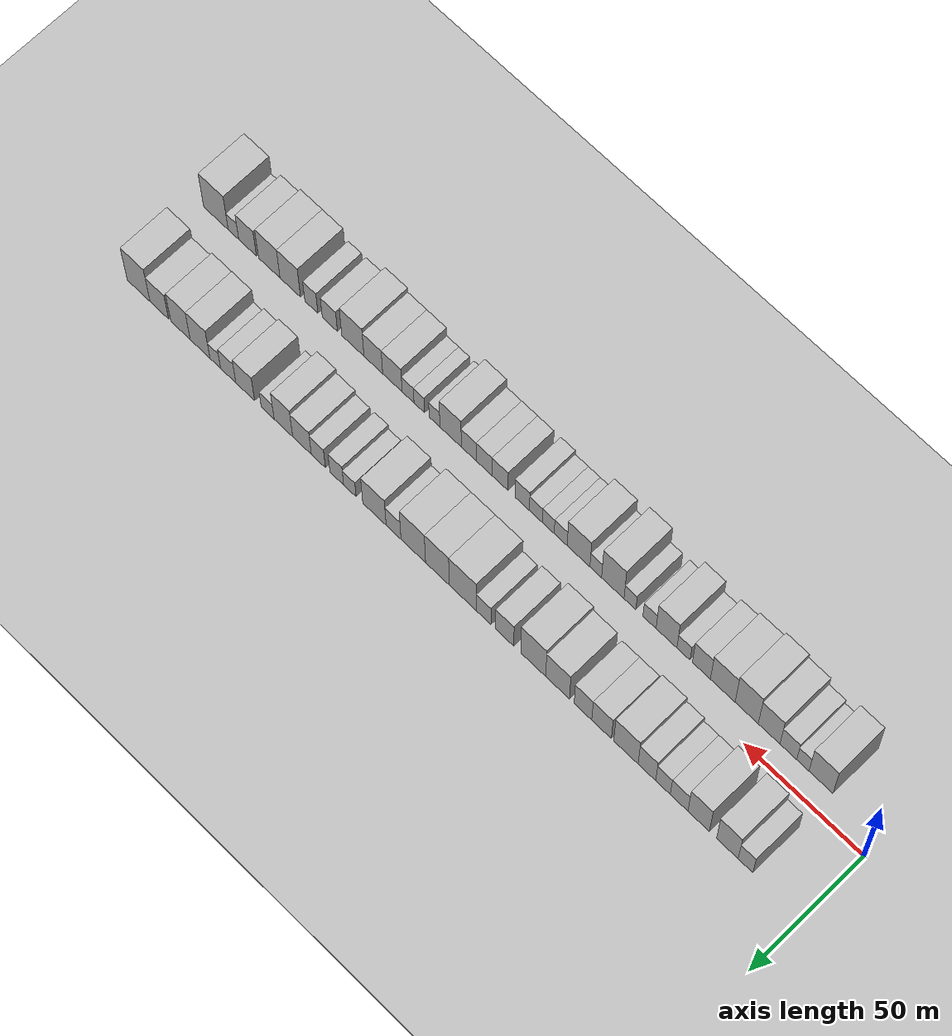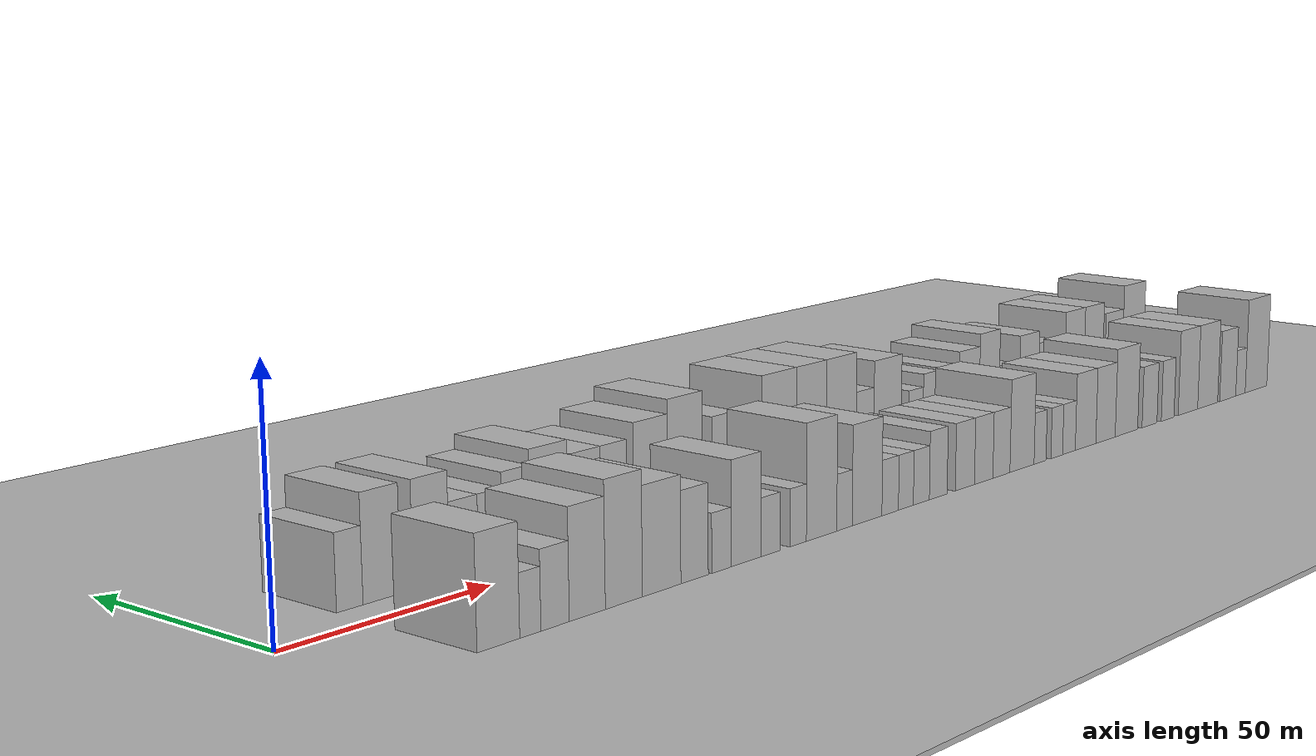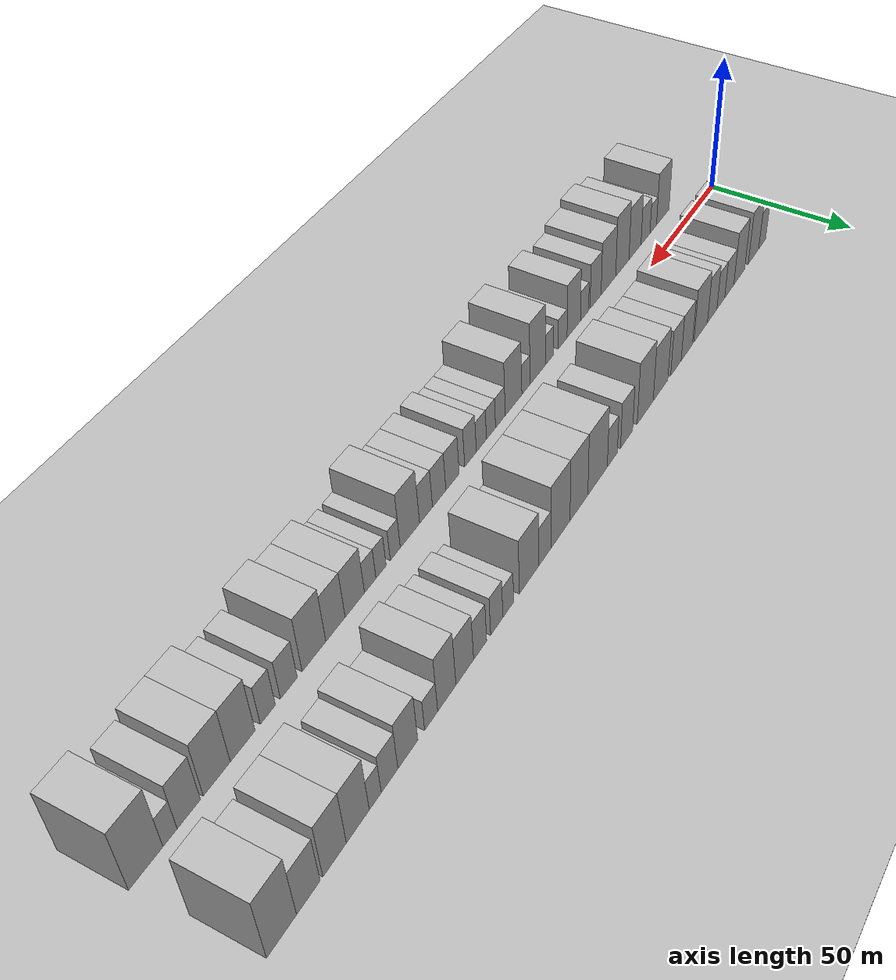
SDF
<?xml version="1.0" encoding="utf-8"?>

<sdf version="1.6">

   <world name="default">

      <gui fullscreen="0">

         <camera name="user_camera">

            <pose>-15 0 4.57585 0 0 0</pose>

            <view_controller>orbit</view_controller>

         </camera>

      </gui>

      <scene>

         <sky>

           <clouds>

             <speed>12</speed>

           </clouds>

         </sky>

         <ambient>0.4 0.4 0.4 1</ambient>

         <background>0.7 0.7 0.7 1</background>

         <shadows>1</shadows>

      </scene>

      <gravity>0 0 -9.8066</gravity>

      <magnetic_field>6e-06 2.3e-05 -4.2e-05</magnetic_field>

      <physics default="0" name="default_physics" type="ode">

         <ode>

            <solver>

               <type>quick</type>

               <iters>10</iters>

               <sor>1.0</sor>

               <use_dynamic_moi_rescaling>0</use_dynamic_moi_rescaling>

            </solver>

            <constraints>

               <cfm>0</cfm>

               <erp>0.2</erp>

               <contact_max_correcting_vel>100</contact_max_correcting_vel>

               <contact_surface_layer>0.001</contact_surface_layer>

            </constraints>

         </ode>

         <max_step_size>0.004</max_step_size>

         <real_time_factor>1</real_time_factor>

         <real_time_update_rate>250</real_time_update_rate>

      </physics>

      <light name="sun" type="directional">

         <cast_shadows>1</cast_shadows>

         <pose>0 0 10 0 0 0</pose>

         <diffuse>0.8 0.8 0.8 1</diffuse>

         <specular>0.2 0.2 0.2 1</specular>

         <attenuation>

            <range>1000</range>

            <constant>0.9</constant>

            <linear>0.01</linear>

            <quadratic>0.001</quadratic>

         </attenuation>

         <direction>-0.5 0.1 -0.9</direction>

      </light>

      <include>

         <name>ground_plane_1</name>

         <uri>model://HANNAS_ground_plane</uri>

         <pose>0 0 0  0 0 0</pose>

      </include>

      <include>

         <name>ground_plane_2</name>

         <uri>model://HANNAS_ground_plane</uri>

         <pose>100 0 0  0 0 0</pose>

      </include>

      <model name="building_1">

         <static>1</static>

         <pose frame="">23.0567 17.5000 0 0.000000 0.000000 1.570796</pose>

         <link name="link">

            <pose frame="">0 0 7.50 0 0 0</pose>

            <collision name="collision">

               <geometry>

                  <box>

                     <size>20.0000 6.1135 15.0000</size>

                  </box>

               </geometry>

               <max_contacts>10</max_contacts>

               <surface>

                  <contact>

                     <ode/>

                  </contact>

                  <bounce/>

                  <friction>

                     <torsional>

                        <ode/>

                     </torsional>

                     <ode/>

                  </friction>

               </surface>

            </collision>

            <visual name="visual">

               <cast_shadows>0</cast_shadows>

               <geometry>

                  <box>

                     <size>20.0000 6.1135 15.0000</size>

                  </box>

               </geometry>

               <material>

                  <script>

                     <uri>model://HANNAS_wall/materials/scripts</uri>

                     <uri>model://HANNAS_wall/materials/textures</uri>

                     <name>vrc/HANNAS_wall</name>

                  </script>

               </material>

            </visual>

            <self_collide>0</self_collide>

            <enable_wind>0</enable_wind>

            <kinematic>0</kinematic>

         </link>

      </model>

      <model name="building_2">

         <static>1</static>

         <pose frame="">30.5935 17.5000 0 0.000000 0.000000 1.570796</pose>

         <link name="link">

            <pose frame="">0 0 10.50 0 0 0</pose>

            <collision name="collision">

               <geometry>

                  <box>

                     <size>20.0000 8.9601 21.0000</size>

                  </box>

               </geometry>

               <max_contacts>10</max_contacts>

               <surface>

                  <contact>

                     <ode/>

                  </contact>

                  <bounce/>

                  <friction>

                     <torsional>

                        <ode/>

                     </torsional>

                     <ode/>

                  </friction>

               </surface>

            </collision>

            <visual name="visual">

               <cast_shadows>0</cast_shadows>

               <geometry>

                  <box>

                     <size>20.0000 8.9601 21.0000</size>

                  </box>

               </geometry>

               <material>

                  <script>

                     <uri>model://HANNAS_wall/materials/scripts</uri>

                     <uri>model://HANNAS_wall/materials/textures</uri>

                     <name>vrc/HANNAS_wall</name>

                  </script>

               </material>

            </visual>

            <self_collide>0</self_collide>

            <enable_wind>0</enable_wind>

            <kinematic>0</kinematic>

         </link>

      </model>

      <model name="building_3">

         <static>1</static>

         <pose frame="">42.5482 17.5000 0 0.000000 0.000000 1.570796</pose>

         <link name="link">

            <pose frame="">0 0 10.50 0 0 0</pose>

            <collision name="collision">

               <geometry>

                  <box>

                     <size>20.0000 8.9492 21.0000</size>

                  </box>

               </geometry>

               <max_contacts>10</max_contacts>

               <surface>

                  <contact>

                     <ode/>

                  </contact>

                  <bounce/>

                  <friction>

                     <torsional>

                        <ode/>

                     </torsional>

                     <ode/>

                  </friction>

               </surface>

            </collision>

            <visual name="visual">

               <cast_shadows>0</cast_shadows>

               <geometry>

                  <box>

                     <size>20.0000 8.9492 21.0000</size>

                  </box>

               </geometry>

               <material>

                  <script>

                     <uri>model://HANNAS_wall/materials/scripts</uri>

                     <uri>model://HANNAS_wall/materials/textures</uri>

                     <name>vrc/HANNAS_wall</name>

                  </script>

               </material>

            </visual>

            <self_collide>0</self_collide>

            <enable_wind>0</enable_wind>

            <kinematic>0</kinematic>

         </link>

      </model>

      <model name="building_4">

         <static>1</static>

         <pose frame="">50.7129 17.5000 0 0.000000 0.000000 1.570796</pose>

         <link name="link">

            <pose frame="">0 0 7.50 0 0 0</pose>

            <collision name="collision">

               <geometry>

                  <box>

                     <size>20.0000 7.3801 15.0000</size>

                  </box>

               </geometry>

               <max_contacts>10</max_contacts>

               <surface>

                  <contact>

                     <ode/>

                  </contact>

                  <bounce/>

                  <friction>

                     <torsional>

                        <ode/>

                     </torsional>

                     <ode/>

                  </friction>

               </surface>

            </collision>

            <visual name="visual">

               <cast_shadows>0</cast_shadows>

               <geometry>

                  <box>

                     <size>20.0000 7.3801 15.0000</size>

                  </box>

               </geometry>

               <material>

                  <script>

                     <uri>model://HANNAS_wall/materials/scripts</uri>

                     <uri>model://HANNAS_wall/materials/textures</uri>

                     <name>vrc/HANNAS_wall</name>

                  </script>

               </material>

            </visual>

            <self_collide>0</self_collide>

            <enable_wind>0</enable_wind>

            <kinematic>0</kinematic>

         </link>

      </model>

      <model name="building_5">

         <static>1</static>

         <pose frame="">57.4828 17.5000 0 0.000000 0.000000 1.570796</pose>

         <link name="link">

            <pose frame="">0 0 7.50 0 0 0</pose>

            <collision name="collision">

               <geometry>

                  <box>

                     <size>20.0000 6.1598 15.0000</size>

                  </box>

               </geometry>

               <max_contacts>10</max_contacts>

               <surface>

                  <contact>

                     <ode/>

                  </contact>

                  <bounce/>

                  <friction>

                     <torsional>

                        <ode/>

                     </torsional>

                     <ode/>

                  </friction>

               </surface>

            </collision>

            <visual name="visual">

               <cast_shadows>0</cast_shadows>

               <geometry>

                  <box>

                     <size>20.0000 6.1598 15.0000</size>

                  </box>

               </geometry>

               <material>

                  <script>

                     <uri>model://HANNAS_wall/materials/scripts</uri>

                     <uri>model://HANNAS_wall/materials/textures</uri>

                     <name>vrc/HANNAS_wall</name>

                  </script>

               </material>

            </visual>

            <self_collide>0</self_collide>

            <enable_wind>0</enable_wind>

            <kinematic>0</kinematic>

         </link>

      </model>

      <model name="building_6">

         <static>1</static>

         <pose frame="">64.2655 17.5000 0 0.000000 0.000000 1.570796</pose>

         <link name="link">

            <pose frame="">0 0 9.00 0 0 0</pose>

            <collision name="collision">

               <geometry>

                  <box>

                     <size>20.0000 7.4056 18.0000</size>

                  </box>

               </geometry>

               <max_contacts>10</max_contacts>

               <surface>

                  <contact>

                     <ode/>

                  </contact>

                  <bounce/>

                  <friction>

                     <torsional>

                        <ode/>

                     </torsional>

                     <ode/>

                  </friction>

               </surface>

            </collision>

            <visual name="visual">

               <cast_shadows>0</cast_shadows>

               <geometry>

                  <box>

                     <size>20.0000 7.4056 18.0000</size>

                  </box>

               </geometry>

               <material>

                  <script>

                     <uri>model://HANNAS_wall/materials/scripts</uri>

                     <uri>model://HANNAS_wall/materials/textures</uri>

                     <name>vrc/HANNAS_wall</name>

                  </script>

               </material>

            </visual>

            <self_collide>0</self_collide>

            <enable_wind>0</enable_wind>

            <kinematic>0</kinematic>

         </link>

      </model>

      <model name="building_7">

         <static>1</static>

         <pose frame="">73.1380 17.5000 0 0.000000 0.000000 1.570796</pose>

         <link name="link">

            <pose frame="">0 0 10.50 0 0 0</pose>

            <collision name="collision">

               <geometry>

                  <box>

                     <size>20.0000 10.3393 21.0000</size>

                  </box>

               </geometry>

               <max_contacts>10</max_contacts>

               <surface>

                  <contact>

                     <ode/>

                  </contact>

                  <bounce/>

                  <friction>

                     <torsional>

                        <ode/>

                     </torsional>

                     <ode/>

                  </friction>

               </surface>

            </collision>

            <visual name="visual">

               <cast_shadows>0</cast_shadows>

               <geometry>

                  <box>

                     <size>20.0000 10.3393 21.0000</size>

                  </box>

               </geometry>

               <material>

                  <script>

                     <uri>model://HANNAS_wall/materials/scripts</uri>

                     <uri>model://HANNAS_wall/materials/textures</uri>

                     <name>vrc/HANNAS_wall</name>

                  </script>

               </material>

            </visual>

            <self_collide>0</self_collide>

            <enable_wind>0</enable_wind>

            <kinematic>0</kinematic>

         </link>

      </model>

      <model name="building_8">

         <static>1</static>

         <pose frame="">83.4733 17.5000 0 0.000000 0.000000 1.570796</pose>

         <link name="link">

            <pose frame="">0 0 9.00 0 0 0</pose>

            <collision name="collision">

               <geometry>

                  <box>

                     <size>20.0000 8.3312 18.0000</size>

                  </box>

               </geometry>

               <max_contacts>10</max_contacts>

               <surface>

                  <contact>

                     <ode/>

                  </contact>

                  <bounce/>

                  <friction>

                     <torsional>

                        <ode/>

                     </torsional>

                     <ode/>

                  </friction>

               </surface>

            </collision>

            <visual name="visual">

               <cast_shadows>0</cast_shadows>

               <geometry>

                  <box>

                     <size>20.0000 8.3312 18.0000</size>

                  </box>

               </geometry>

               <material>

                  <script>

                     <uri>model://HANNAS_wall/materials/scripts</uri>

                     <uri>model://HANNAS_wall/materials/textures</uri>

                     <name>vrc/HANNAS_wall</name>

                  </script>

               </material>

            </visual>

            <self_collide>0</self_collide>

            <enable_wind>0</enable_wind>

            <kinematic>0</kinematic>

         </link>

      </model>

      <model name="building_9">

         <static>1</static>

         <pose frame="">91.4008 17.5000 0 0.000000 0.000000 1.570796</pose>

         <link name="link">

            <pose frame="">0 0 9.00 0 0 0</pose>

            <collision name="collision">

               <geometry>

                  <box>

                     <size>20.0000 7.5239 18.0000</size>

                  </box>

               </geometry>

               <max_contacts>10</max_contacts>

               <surface>

                  <contact>

                     <ode/>

                  </contact>

                  <bounce/>

                  <friction>

                     <torsional>

                        <ode/>

                     </torsional>

                     <ode/>

                  </friction>

               </surface>

            </collision>

            <visual name="visual">

               <cast_shadows>0</cast_shadows>

               <geometry>

                  <box>

                     <size>20.0000 7.5239 18.0000</size>

                  </box>

               </geometry>

               <material>

                  <script>

                     <uri>model://HANNAS_wall/materials/scripts</uri>

                     <uri>model://HANNAS_wall/materials/textures</uri>

                     <name>vrc/HANNAS_wall</name>

                  </script>

               </material>

            </visual>

            <self_collide>0</self_collide>

            <enable_wind>0</enable_wind>

            <kinematic>0</kinematic>

         </link>

      </model>

      <model name="building_10">

         <static>1</static>

         <pose frame="">102.2563 17.5000 0 0.000000 0.000000 1.570796</pose>

         <link name="link">

            <pose frame="">0 0 10.50 0 0 0</pose>

            <collision name="collision">

               <geometry>

                  <box>

                     <size>20.0000 10.1870 21.0000</size>

                  </box>

               </geometry>

               <max_contacts>10</max_contacts>

               <surface>

                  <contact>

                     <ode/>

                  </contact>

                  <bounce/>

                  <friction>

                     <torsional>

                        <ode/>

                     </torsional>

                     <ode/>

                  </friction>

               </surface>

            </collision>

            <visual name="visual">

               <cast_shadows>0</cast_shadows>

               <geometry>

                  <box>

                     <size>20.0000 10.1870 21.0000</size>

                  </box>

               </geometry>

               <material>

                  <script>

                     <uri>model://HANNAS_wall/materials/scripts</uri>

                     <uri>model://HANNAS_wall/materials/textures</uri>

                     <name>vrc/HANNAS_wall</name>

                  </script>

               </material>

            </visual>

            <self_collide>0</self_collide>

            <enable_wind>0</enable_wind>

            <kinematic>0</kinematic>

         </link>

      </model>

      <model name="building_11">

         <static>1</static>

         <pose frame="">112.7394 17.5000 0 0.000000 0.000000 1.570796</pose>

         <link name="link">

            <pose frame="">0 0 12.00 0 0 0</pose>

            <collision name="collision">

               <geometry>

                  <box>

                     <size>20.0000 10.7792 24.0000</size>

                  </box>

               </geometry>

               <max_contacts>10</max_contacts>

               <surface>

                  <contact>

                     <ode/>

                  </contact>

                  <bounce/>

                  <friction>

                     <torsional>

                        <ode/>

                     </torsional>

                     <ode/>

                  </friction>

               </surface>

            </collision>

            <visual name="visual">

               <cast_shadows>0</cast_shadows>

               <geometry>

                  <box>

                     <size>20.0000 10.7792 24.0000</size>

                  </box>

               </geometry>

               <material>

                  <script>

                     <uri>model://HANNAS_wall/materials/scripts</uri>

                     <uri>model://HANNAS_wall/materials/textures</uri>

                     <name>vrc/HANNAS_wall</name>

                  </script>

               </material>

            </visual>

            <self_collide>0</self_collide>

            <enable_wind>0</enable_wind>

            <kinematic>0</kinematic>

         </link>

      </model>

      <model name="building_12">

         <static>1</static>

         <pose frame="">125.0622 17.5000 0 0.000000 0.000000 1.570796</pose>

         <link name="link">

            <pose frame="">0 0 9.00 0 0 0</pose>

            <collision name="collision">

               <geometry>

                  <box>

                     <size>20.0000 7.8665 18.0000</size>

                  </box>

               </geometry>

               <max_contacts>10</max_contacts>

               <surface>

                  <contact>

                     <ode/>

                  </contact>

                  <bounce/>

                  <friction>

                     <torsional>

                        <ode/>

                     </torsional>

                     <ode/>

                  </friction>

               </surface>

            </collision>

            <visual name="visual">

               <cast_shadows>0</cast_shadows>

               <geometry>

                  <box>

                     <size>20.0000 7.8665 18.0000</size>

                  </box>

               </geometry>

               <material>

                  <script>

                     <uri>model://HANNAS_wall/materials/scripts</uri>

                     <uri>model://HANNAS_wall/materials/textures</uri>

                     <name>vrc/HANNAS_wall</name>

                  </script>

               </material>

            </visual>

            <self_collide>0</self_collide>

            <enable_wind>0</enable_wind>

            <kinematic>0</kinematic>

         </link>

      </model>

      <model name="building_13">

         <static>1</static>

         <pose frame="">134.1541 17.5000 0 0.000000 0.000000 1.570796</pose>

         <link name="link">

            <pose frame="">0 0 7.50 0 0 0</pose>

            <collision name="collision">

               <geometry>

                  <box>

                     <size>20.0000 6.3173 15.0000</size>

                  </box>

               </geometry>

               <max_contacts>10</max_contacts>

               <surface>

                  <contact>

                     <ode/>

                  </contact>

                  <bounce/>

                  <friction>

                     <torsional>

                        <ode/>

                     </torsional>

                     <ode/>

                  </friction>

               </surface>

            </collision>

            <visual name="visual">

               <cast_shadows>0</cast_shadows>

               <geometry>

                  <box>

                     <size>20.0000 6.3173 15.0000</size>

                  </box>

               </geometry>

               <material>

                  <script>

                     <uri>model://HANNAS_wall/materials/scripts</uri>

                     <uri>model://HANNAS_wall/materials/textures</uri>

                     <name>vrc/HANNAS_wall</name>

                  </script>

               </material>

            </visual>

            <self_collide>0</self_collide>

            <enable_wind>0</enable_wind>

            <kinematic>0</kinematic>

         </link>

      </model>

      <model name="building_14">

         <static>1</static>

         <pose frame="">143.2577 17.5000 0 0.000000 0.000000 1.570796</pose>

         <link name="link">

            <pose frame="">0 0 12.00 0 0 0</pose>

            <collision name="collision">

               <geometry>

                  <box>

                     <size>20.0000 11.8899 24.0000</size>

                  </box>

               </geometry>

               <max_contacts>10</max_contacts>

               <surface>

                  <contact>

                     <ode/>

                  </contact>

                  <bounce/>

                  <friction>

                     <torsional>

                        <ode/>

                     </torsional>

                     <ode/>

                  </friction>

               </surface>

            </collision>

            <visual name="visual">

               <cast_shadows>0</cast_shadows>

               <geometry>

                  <box>

                     <size>20.0000 11.8899 24.0000</size>

                  </box>

               </geometry>

               <material>

                  <script>

                     <uri>model://HANNAS_wall/materials/scripts</uri>

                     <uri>model://HANNAS_wall/materials/textures</uri>

                     <name>vrc/HANNAS_wall</name>

                  </script>

               </material>

            </visual>

            <self_collide>0</self_collide>

            <enable_wind>0</enable_wind>

            <kinematic>0</kinematic>

         </link>

      </model>

      <model name="building_15">

         <static>1</static>

         <pose frame="">154.4474 17.5000 0 0.000000 0.000000 1.570796</pose>

         <link name="link">

            <pose frame="">0 0 12.00 0 0 0</pose>

            <collision name="collision">

               <geometry>

                  <box>

                     <size>20.0000 10.4894 24.0000</size>

                  </box>

               </geometry>

               <max_contacts>10</max_contacts>

               <surface>

                  <contact>

                     <ode/>

                  </contact>

                  <bounce/>

                  <friction>

                     <torsional>

                        <ode/>

                     </torsional>

                     <ode/>

                  </friction>

               </surface>

            </collision>

            <visual name="visual">

               <cast_shadows>0</cast_shadows>

               <geometry>

                  <box>

                     <size>20.0000 10.4894 24.0000</size>

                  </box>

               </geometry>

               <material>

                  <script>

                     <uri>model://HANNAS_wall/materials/scripts</uri>

                     <uri>model://HANNAS_wall/materials/textures</uri>

                     <name>vrc/HANNAS_wall</name>

                  </script>

               </material>

            </visual>

            <self_collide>0</self_collide>

            <enable_wind>0</enable_wind>

            <kinematic>0</kinematic>

         </link>

      </model>

      <model name="building_16">

         <static>1</static>

         <pose frame="">165.1244 17.5000 0 0.000000 0.000000 1.570796</pose>

         <link name="link">

            <pose frame="">0 0 12.00 0 0 0</pose>

            <collision name="collision">

               <geometry>

                  <box>

                     <size>20.0000 10.8648 24.0000</size>

                  </box>

               </geometry>

               <max_contacts>10</max_contacts>

               <surface>

                  <contact>

                     <ode/>

                  </contact>

                  <bounce/>

                  <friction>

                     <torsional>

                        <ode/>

                     </torsional>

                     <ode/>

                  </friction>

               </surface>

            </collision>

            <visual name="visual">

               <cast_shadows>0</cast_shadows>

               <geometry>

                  <box>

                     <size>20.0000 10.8648 24.0000</size>

                  </box>

               </geometry>

               <material>

                  <script>

                     <uri>model://HANNAS_wall/materials/scripts</uri>

                     <uri>model://HANNAS_wall/materials/textures</uri>

                     <name>vrc/HANNAS_wall</name>

                  </script>

               </material>

            </visual>

            <self_collide>0</self_collide>

            <enable_wind>0</enable_wind>

            <kinematic>0</kinematic>

         </link>

      </model>

      <model name="building_17">

         <static>1</static>

         <pose frame="">173.8574 17.5000 0 0.000000 0.000000 1.570796</pose>

         <link name="link">

            <pose frame="">0 0 7.50 0 0 0</pose>

            <collision name="collision">

               <geometry>

                  <box>

                     <size>20.0000 6.6013 15.0000</size>

                  </box>

               </geometry>

               <max_contacts>10</max_contacts>

               <surface>

                  <contact>

                     <ode/>

                  </contact>

                  <bounce/>

                  <friction>

                     <torsional>

                        <ode/>

                     </torsional>

                     <ode/>

                  </friction>

               </surface>

            </collision>

            <visual name="visual">

               <cast_shadows>0</cast_shadows>

               <geometry>

                  <box>

                     <size>20.0000 6.6013 15.0000</size>

                  </box>

               </geometry>

               <material>

                  <script>

                     <uri>model://HANNAS_wall/materials/scripts</uri>

                     <uri>model://HANNAS_wall/materials/textures</uri>

                     <name>vrc/HANNAS_wall</name>

                  </script>

               </material>

            </visual>

            <self_collide>0</self_collide>

            <enable_wind>0</enable_wind>

            <kinematic>0</kinematic>

         </link>

      </model>

      <model name="building_18">

         <static>1</static>

         <pose frame="">182.3586 17.5000 0 0.000000 0.000000 1.570796</pose>

         <link name="link">

            <pose frame="">0 0 10.50 0 0 0</pose>

            <collision name="collision">

               <geometry>

                  <box>

                     <size>20.0000 10.4010 21.0000</size>

                  </box>

               </geometry>

               <max_contacts>10</max_contacts>

               <surface>

                  <contact>

                     <ode/>

                  </contact>

                  <bounce/>

                  <friction>

                     <torsional>

                        <ode/>

                     </torsional>

                     <ode/>

                  </friction>

               </surface>

            </collision>

            <visual name="visual">

               <cast_shadows>0</cast_shadows>

               <geometry>

                  <box>

                     <size>20.0000 10.4010 21.0000</size>

                  </box>

               </geometry>

               <material>

                  <script>

                     <uri>model://HANNAS_wall/materials/scripts</uri>

                     <uri>model://HANNAS_wall/materials/textures</uri>

                     <name>vrc/HANNAS_wall</name>

                  </script>

               </material>

            </visual>

            <self_collide>0</self_collide>

            <enable_wind>0</enable_wind>

            <kinematic>0</kinematic>

         </link>

      </model>

      <model name="building_19">

         <static>1</static>

         <pose frame="">193.3541 17.5000 0 0.000000 0.000000 1.570796</pose>

         <link name="link">

            <pose frame="">0 0 6.00 0 0 0</pose>

            <collision name="collision">

               <geometry>

                  <box>

                     <size>20.0000 5.5900 12.0000</size>

                  </box>

               </geometry>

               <max_contacts>10</max_contacts>

               <surface>

                  <contact>

                     <ode/>

                  </contact>

                  <bounce/>

                  <friction>

                     <torsional>

                        <ode/>

                     </torsional>

                     <ode/>

                  </friction>

               </surface>

            </collision>

            <visual name="visual">

               <cast_shadows>0</cast_shadows>

               <geometry>

                  <box>

                     <size>20.0000 5.5900 12.0000</size>

                  </box>

               </geometry>

               <material>

                  <script>

                     <uri>model://HANNAS_wall/materials/scripts</uri>

                     <uri>model://HANNAS_wall/materials/textures</uri>

                     <name>vrc/HANNAS_wall</name>

                  </script>

               </material>

            </visual>

            <self_collide>0</self_collide>

            <enable_wind>0</enable_wind>

            <kinematic>0</kinematic>

         </link>

      </model>

      <model name="building_20">

         <static>1</static>

         <pose frame="">199.2261 17.5000 0 0.000000 0.000000 1.570796</pose>

         <link name="link">

            <pose frame="">0 0 7.50 0 0 0</pose>

            <collision name="collision">

               <geometry>

                  <box>

                     <size>20.0000 6.1541 15.0000</size>

                  </box>

               </geometry>

               <max_contacts>10</max_contacts>

               <surface>

                  <contact>

                     <ode/>

                  </contact>

                  <bounce/>

                  <friction>

                     <torsional>

                        <ode/>

                     </torsional>

                     <ode/>

                  </friction>

               </surface>

            </collision>

            <visual name="visual">

               <cast_shadows>0</cast_shadows>

               <geometry>

                  <box>

                     <size>20.0000 6.1541 15.0000</size>

                  </box>

               </geometry>

               <material>

                  <script>

                     <uri>model://HANNAS_wall/materials/scripts</uri>

                     <uri>model://HANNAS_wall/materials/textures</uri>

                     <name>vrc/HANNAS_wall</name>

                  </script>

               </material>

            </visual>

            <self_collide>0</self_collide>

            <enable_wind>0</enable_wind>

            <kinematic>0</kinematic>

         </link>

      </model>

      <model name="building_21">

         <static>1</static>

         <pose frame="">207.4873 17.5000 0 0.000000 0.000000 1.570796</pose>

         <link name="link">

            <pose frame="">0 0 7.50 0 0 0</pose>

            <collision name="collision">

               <geometry>

                  <box>

                     <size>20.0000 6.3683 15.0000</size>

                  </box>

               </geometry>

               <max_contacts>10</max_contacts>

               <surface>

                  <contact>

                     <ode/>

                  </contact>

                  <bounce/>

                  <friction>

                     <torsional>

                        <ode/>

                     </torsional>

                     <ode/>

                  </friction>

               </surface>

            </collision>

            <visual name="visual">

               <cast_shadows>0</cast_shadows>

               <geometry>

                  <box>

                     <size>20.0000 6.3683 15.0000</size>

                  </box>

               </geometry>

               <material>

                  <script>

                     <uri>model://HANNAS_wall/materials/scripts</uri>

                     <uri>model://HANNAS_wall/materials/textures</uri>

                     <name>vrc/HANNAS_wall</name>

                  </script>

               </material>

            </visual>

            <self_collide>0</self_collide>

            <enable_wind>0</enable_wind>

            <kinematic>0</kinematic>

         </link>

      </model>

      <model name="building_22">

         <static>1</static>

         <pose frame="">214.8845 17.5000 0 0.000000 0.000000 1.570796</pose>

         <link name="link">

            <pose frame="">0 0 9.00 0 0 0</pose>

            <collision name="collision">

               <geometry>

                  <box>

                     <size>20.0000 8.4260 18.0000</size>

                  </box>

               </geometry>

               <max_contacts>10</max_contacts>

               <surface>

                  <contact>

                     <ode/>

                  </contact>

                  <bounce/>

                  <friction>

                     <torsional>

                        <ode/>

                     </torsional>

                     <ode/>

                  </friction>

               </surface>

            </collision>

            <visual name="visual">

               <cast_shadows>0</cast_shadows>

               <geometry>

                  <box>

                     <size>20.0000 8.4260 18.0000</size>

                  </box>

               </geometry>

               <material>

                  <script>

                     <uri>model://HANNAS_wall/materials/scripts</uri>

                     <uri>model://HANNAS_wall/materials/textures</uri>

                     <name>vrc/HANNAS_wall</name>

                  </script>

               </material>

            </visual>

            <self_collide>0</self_collide>

            <enable_wind>0</enable_wind>

            <kinematic>0</kinematic>

         </link>

      </model>

      <model name="building_23">

         <static>1</static>

         <pose frame="">223.3157 17.5000 0 0.000000 0.000000 1.570796</pose>

         <link name="link">

            <pose frame="">0 0 10.50 0 0 0</pose>

            <collision name="collision">

               <geometry>

                  <box>

                     <size>20.0000 8.4365 21.0000</size>

                  </box>

               </geometry>

               <max_contacts>10</max_contacts>

               <surface>

                  <contact>

                     <ode/>

                  </contact>

                  <bounce/>

                  <friction>

                     <torsional>

                        <ode/>

                     </torsional>

                     <ode/>

                  </friction>

               </surface>

            </collision>

            <visual name="visual">

               <cast_shadows>0</cast_shadows>

               <geometry>

                  <box>

                     <size>20.0000 8.4365 21.0000</size>

                  </box>

               </geometry>

               <material>

                  <script>

                     <uri>model://HANNAS_wall/materials/scripts</uri>

                     <uri>model://HANNAS_wall/materials/textures</uri>

                     <name>vrc/HANNAS_wall</name>

                  </script>

               </material>

            </visual>

            <self_collide>0</self_collide>

            <enable_wind>0</enable_wind>

            <kinematic>0</kinematic>

         </link>

      </model>

      <model name="building_24">

         <static>1</static>

         <pose frame="">230.4687 17.5000 0 0.000000 0.000000 1.570796</pose>

         <link name="link">

            <pose frame="">0 0 6.00 0 0 0</pose>

            <collision name="collision">

               <geometry>

                  <box>

                     <size>20.0000 5.8695 12.0000</size>

                  </box>

               </geometry>

               <max_contacts>10</max_contacts>

               <surface>

                  <contact>

                     <ode/>

                  </contact>

                  <bounce/>

                  <friction>

                     <torsional>

                        <ode/>

                     </torsional>

                     <ode/>

                  </friction>

               </surface>

            </collision>

            <visual name="visual">

               <cast_shadows>0</cast_shadows>

               <geometry>

                  <box>

                     <size>20.0000 5.8695 12.0000</size>

                  </box>

               </geometry>

               <material>

                  <script>

                     <uri>model://HANNAS_wall/materials/scripts</uri>

                     <uri>model://HANNAS_wall/materials/textures</uri>

                     <name>vrc/HANNAS_wall</name>

                  </script>

               </material>

            </visual>

            <self_collide>0</self_collide>

            <enable_wind>0</enable_wind>

            <kinematic>0</kinematic>

         </link>

      </model>

      <model name="building_25">

         <static>1</static>

         <pose frame="">240.7069 17.5000 0 0.000000 0.000000 1.570796</pose>

         <link name="link">

            <pose frame="">0 0 9.00 0 0 0</pose>

            <collision name="collision">

               <geometry>

                  <box>

                     <size>20.0000 8.6068 18.0000</size>

                  </box>

               </geometry>

               <max_contacts>10</max_contacts>

               <surface>

                  <contact>

                     <ode/>

                  </contact>

                  <bounce/>

                  <friction>

                     <torsional>

                        <ode/>

                     </torsional>

                     <ode/>

                  </friction>

               </surface>

            </collision>

            <visual name="visual">

               <cast_shadows>0</cast_shadows>

               <geometry>

                  <box>

                     <size>20.0000 8.6068 18.0000</size>

                  </box>

               </geometry>

               <material>

                  <script>

                     <uri>model://HANNAS_wall/materials/scripts</uri>

                     <uri>model://HANNAS_wall/materials/textures</uri>

                     <name>vrc/HANNAS_wall</name>

                  </script>

               </material>

            </visual>

            <self_collide>0</self_collide>

            <enable_wind>0</enable_wind>

            <kinematic>0</kinematic>

         </link>

      </model>

      <model name="building_26">

         <static>1</static>

         <pose frame="">248.5009 17.5000 0 0.000000 0.000000 1.570796</pose>

         <link name="link">

            <pose frame="">0 0 7.50 0 0 0</pose>

            <collision name="collision">

               <geometry>

                  <box>

                     <size>20.0000 6.9813 15.0000</size>

                  </box>

               </geometry>

               <max_contacts>10</max_contacts>

               <surface>

                  <contact>

                     <ode/>

                  </contact>

                  <bounce/>

                  <friction>

                     <torsional>

                        <ode/>

                     </torsional>

                     <ode/>

                  </friction>

               </surface>

            </collision>

            <visual name="visual">

               <cast_shadows>0</cast_shadows>

               <geometry>

                  <box>

                     <size>20.0000 6.9813 15.0000</size>

                  </box>

               </geometry>

               <material>

                  <script>

                     <uri>model://HANNAS_wall/materials/scripts</uri>

                     <uri>model://HANNAS_wall/materials/textures</uri>

                     <name>vrc/HANNAS_wall</name>

                  </script>

               </material>

            </visual>

            <self_collide>0</self_collide>

            <enable_wind>0</enable_wind>

            <kinematic>0</kinematic>

         </link>

      </model>

      <model name="building_27">

         <static>1</static>

         <pose frame="">254.4521 17.5000 0 0.000000 0.000000 1.570796</pose>

         <link name="link">

            <pose frame="">0 0 6.00 0 0 0</pose>

            <collision name="collision">

               <geometry>

                  <box>

                     <size>20.0000 4.9211 12.0000</size>

                  </box>

               </geometry>

               <max_contacts>10</max_contacts>

               <surface>

                  <contact>

                     <ode/>

                  </contact>

                  <bounce/>

                  <friction>

                     <torsional>

                        <ode/>

                     </torsional>

                     <ode/>

                  </friction>

               </surface>

            </collision>

            <visual name="visual">

               <cast_shadows>0</cast_shadows>

               <geometry>

                  <box>

                     <size>20.0000 4.9211 12.0000</size>

                  </box>

               </geometry>

               <material>

                  <script>

                     <uri>model://HANNAS_wall/materials/scripts</uri>

                     <uri>model://HANNAS_wall/materials/textures</uri>

                     <name>vrc/HANNAS_wall</name>

                  </script>

               </material>

            </visual>

            <self_collide>0</self_collide>

            <enable_wind>0</enable_wind>

            <kinematic>0</kinematic>

         </link>

      </model>

      <model name="building_28">

         <static>1</static>

         <pose frame="">261.4727 17.5000 0 0.000000 0.000000 1.570796</pose>

         <link name="link">

            <pose frame="">0 0 10.50 0 0 0</pose>

            <collision name="collision">

               <geometry>

                  <box>

                     <size>20.0000 9.1201 21.0000</size>

                  </box>

               </geometry>

               <max_contacts>10</max_contacts>

               <surface>

                  <contact>

                     <ode/>

                  </contact>

                  <bounce/>

                  <friction>

                     <torsional>

                        <ode/>

                     </torsional>

                     <ode/>

                  </friction>

               </surface>

            </collision>

            <visual name="visual">

               <cast_shadows>0</cast_shadows>

               <geometry>

                  <box>

                     <size>20.0000 9.1201 21.0000</size>

                  </box>

               </geometry>

               <material>

                  <script>

                     <uri>model://HANNAS_wall/materials/scripts</uri>

                     <uri>model://HANNAS_wall/materials/textures</uri>

                     <name>vrc/HANNAS_wall</name>

                  </script>

               </material>

            </visual>

            <self_collide>0</self_collide>

            <enable_wind>0</enable_wind>

            <kinematic>0</kinematic>

         </link>

      </model>

      <model name="building_29">

         <static>1</static>

         <pose frame="">270.5441 17.5000 0 0.000000 0.000000 1.570796</pose>

         <link name="link">

            <pose frame="">0 0 10.50 0 0 0</pose>

            <collision name="collision">

               <geometry>

                  <box>

                     <size>20.0000 9.0228 21.0000</size>

                  </box>

               </geometry>

               <max_contacts>10</max_contacts>

               <surface>

                  <contact>

                     <ode/>

                  </contact>

                  <bounce/>

                  <friction>

                     <torsional>

                        <ode/>

                     </torsional>

                     <ode/>

                  </friction>

               </surface>

            </collision>

            <visual name="visual">

               <cast_shadows>0</cast_shadows>

               <geometry>

                  <box>

                     <size>20.0000 9.0228 21.0000</size>

                  </box>

               </geometry>

               <material>

                  <script>

                     <uri>model://HANNAS_wall/materials/scripts</uri>

                     <uri>model://HANNAS_wall/materials/textures</uri>

                     <name>vrc/HANNAS_wall</name>

                  </script>

               </material>

            </visual>

            <self_collide>0</self_collide>

            <enable_wind>0</enable_wind>

            <kinematic>0</kinematic>

         </link>

      </model>

      <model name="building_30">

         <static>1</static>

         <pose frame="">280.3954 17.5000 0 0.000000 0.000000 1.570796</pose>

         <link name="link">

            <pose frame="">0 0 9.00 0 0 0</pose>

            <collision name="collision">

               <geometry>

                  <box>

                     <size>20.0000 8.6798 18.0000</size>

                  </box>

               </geometry>

               <max_contacts>10</max_contacts>

               <surface>

                  <contact>

                     <ode/>

                  </contact>

                  <bounce/>

                  <friction>

                     <torsional>

                        <ode/>

                     </torsional>

                     <ode/>

                  </friction>

               </surface>

            </collision>

            <visual name="visual">

               <cast_shadows>0</cast_shadows>

               <geometry>

                  <box>

                     <size>20.0000 8.6798 18.0000</size>

                  </box>

               </geometry>

               <material>

                  <script>

                     <uri>model://HANNAS_wall/materials/scripts</uri>

                     <uri>model://HANNAS_wall/materials/textures</uri>

                     <name>vrc/HANNAS_wall</name>

                  </script>

               </material>

            </visual>

            <self_collide>0</self_collide>

            <enable_wind>0</enable_wind>

            <kinematic>0</kinematic>

         </link>

      </model>

      <model name="building_31">

         <static>1</static>

         <pose frame="">290.0700 17.5000 0 0.000000 0.000000 1.570796</pose>

         <link name="link">

            <pose frame="">0 0 12.00 0 0 0</pose>

            <collision name="collision">

               <geometry>

                  <box>

                     <size>20.0000 10.6693 24.0000</size>

                  </box>

               </geometry>

               <max_contacts>10</max_contacts>

               <surface>

                  <contact>

                     <ode/>

                  </contact>

                  <bounce/>

                  <friction>

                     <torsional>

                        <ode/>

                     </torsional>

                     <ode/>

                  </friction>

               </surface>

            </collision>

            <visual name="visual">

               <cast_shadows>0</cast_shadows>

               <geometry>

                  <box>

                     <size>20.0000 10.6693 24.0000</size>

                  </box>

               </geometry>

               <material>

                  <script>

                     <uri>model://HANNAS_wall/materials/scripts</uri>

                     <uri>model://HANNAS_wall/materials/textures</uri>

                     <name>vrc/HANNAS_wall</name>

                  </script>

               </material>

            </visual>

            <self_collide>0</self_collide>

            <enable_wind>0</enable_wind>

            <kinematic>0</kinematic>

         </link>

      </model>

      <model name="building_32">

         <static>1</static>

         <pose frame="">24.9873 -17.5000 0 0.000000 0.000000 1.570796</pose>

         <link name="link">

            <pose frame="">0 0 10.50 0 0 0</pose>

            <collision name="collision">

               <geometry>

                  <box>

                     <size>20.0000 9.9746 21.0000</size>

                  </box>

               </geometry>

               <max_contacts>10</max_contacts>

               <surface>

                  <contact>

                     <ode/>

                  </contact>

                  <bounce/>

                  <friction>

                     <torsional>

                        <ode/>

                     </torsional>

                     <ode/>

                  </friction>

               </surface>

            </collision>

            <visual name="visual">

               <cast_shadows>0</cast_shadows>

               <geometry>

                  <box>

                     <size>20.0000 9.9746 21.0000</size>

                  </box>

               </geometry>

               <material>

                  <script>

                     <uri>model://HANNAS_wall/materials/scripts</uri>

                     <uri>model://HANNAS_wall/materials/textures</uri>

                     <name>vrc/HANNAS_wall</name>

                  </script>

               </material>

            </visual>

            <self_collide>0</self_collide>

            <enable_wind>0</enable_wind>

            <kinematic>0</kinematic>

         </link>

      </model>

      <model name="building_33">

         <static>1</static>

         <pose frame="">32.5217 -17.5000 0 0.000000 0.000000 1.570796</pose>

         <link name="link">

            <pose frame="">0 0 6.00 0 0 0</pose>

            <collision name="collision">

               <geometry>

                  <box>

                     <size>20.0000 5.0942 12.0000</size>

                  </box>

               </geometry>

               <max_contacts>10</max_contacts>

               <surface>

                  <contact>

                     <ode/>

                  </contact>

                  <bounce/>

                  <friction>

                     <torsional>

                        <ode/>

                     </torsional>

                     <ode/>

                  </friction>

               </surface>

            </collision>

            <visual name="visual">

               <cast_shadows>0</cast_shadows>

               <geometry>

                  <box>

                     <size>20.0000 5.0942 12.0000</size>

                  </box>

               </geometry>

               <material>

                  <script>

                     <uri>model://HANNAS_wall/materials/scripts</uri>

                     <uri>model://HANNAS_wall/materials/textures</uri>

                     <name>vrc/HANNAS_wall</name>

                  </script>

               </material>

            </visual>

            <self_collide>0</self_collide>

            <enable_wind>0</enable_wind>

            <kinematic>0</kinematic>

         </link>

      </model>

      <model name="building_34">

         <static>1</static>

         <pose frame="">38.5519 -17.5000 0 0.000000 0.000000 1.570796</pose>

         <link name="link">

            <pose frame="">0 0 7.50 0 0 0</pose>

            <collision name="collision">

               <geometry>

                  <box>

                     <size>20.0000 6.9662 15.0000</size>

                  </box>

               </geometry>

               <max_contacts>10</max_contacts>

               <surface>

                  <contact>

                     <ode/>

                  </contact>

                  <bounce/>

                  <friction>

                     <torsional>

                        <ode/>

                     </torsional>

                     <ode/>

                  </friction>

               </surface>

            </collision>

            <visual name="visual">

               <cast_shadows>0</cast_shadows>

               <geometry>

                  <box>

                     <size>20.0000 6.9662 15.0000</size>

                  </box>

               </geometry>

               <material>

                  <script>

                     <uri>model://HANNAS_wall/materials/scripts</uri>

                     <uri>model://HANNAS_wall/materials/textures</uri>

                     <name>vrc/HANNAS_wall</name>

                  </script>

               </material>

            </visual>

            <self_collide>0</self_collide>

            <enable_wind>0</enable_wind>

            <kinematic>0</kinematic>

         </link>

      </model>

      <model name="building_35">

         <static>1</static>

         <pose frame="">46.5921 -17.5000 0 0.000000 0.000000 1.570796</pose>

         <link name="link">

            <pose frame="">0 0 10.50 0 0 0</pose>

            <collision name="collision">

               <geometry>

                  <box>

                     <size>20.0000 9.1143 21.0000</size>

                  </box>

               </geometry>

               <max_contacts>10</max_contacts>

               <surface>

                  <contact>

                     <ode/>

                  </contact>

                  <bounce/>

                  <friction>

                     <torsional>

                        <ode/>

                     </torsional>

                     <ode/>

                  </friction>

               </surface>

            </collision>

            <visual name="visual">

               <cast_shadows>0</cast_shadows>

               <geometry>

                  <box>

                     <size>20.0000 9.1143 21.0000</size>

                  </box>

               </geometry>

               <material>

                  <script>

                     <uri>model://HANNAS_wall/materials/scripts</uri>

                     <uri>model://HANNAS_wall/materials/textures</uri>

                     <name>vrc/HANNAS_wall</name>

                  </script>

               </material>

            </visual>

            <self_collide>0</self_collide>

            <enable_wind>0</enable_wind>

            <kinematic>0</kinematic>

         </link>

      </model>

      <model name="building_36">

         <static>1</static>

         <pose frame="">56.0097 -17.5000 0 0.000000 0.000000 1.570796</pose>

         <link name="link">

            <pose frame="">0 0 12.00 0 0 0</pose>

            <collision name="collision">

               <geometry>

                  <box>

                     <size>20.0000 9.7208 24.0000</size>

                  </box>

               </geometry>

               <max_contacts>10</max_contacts>

               <surface>

                  <contact>

                     <ode/>

                  </contact>

                  <bounce/>

                  <friction>

                     <torsional>

                        <ode/>

                     </torsional>

                     <ode/>

                  </friction>

               </surface>

            </collision>

            <visual name="visual">

               <cast_shadows>0</cast_shadows>

               <geometry>

                  <box>

                     <size>20.0000 9.7208 24.0000</size>

                  </box>

               </geometry>

               <material>

                  <script>

                     <uri>model://HANNAS_wall/materials/scripts</uri>

                     <uri>model://HANNAS_wall/materials/textures</uri>

                     <name>vrc/HANNAS_wall</name>

                  </script>

               </material>

            </visual>

            <self_collide>0</self_collide>

            <enable_wind>0</enable_wind>

            <kinematic>0</kinematic>

         </link>

      </model>

      <model name="building_37">

         <static>1</static>

         <pose frame="">66.0737 -17.5000 0 0.000000 0.000000 1.570796</pose>

         <link name="link">

            <pose frame="">0 0 10.50 0 0 0</pose>

            <collision name="collision">

               <geometry>

                  <box>

                     <size>20.0000 10.4071 21.0000</size>

                  </box>

               </geometry>

               <max_contacts>10</max_contacts>

               <surface>

                  <contact>

                     <ode/>

                  </contact>

                  <bounce/>

                  <friction>

                     <torsional>

                        <ode/>

                     </torsional>

                     <ode/>

                  </friction>

               </surface>

            </collision>

            <visual name="visual">

               <cast_shadows>0</cast_shadows>

               <geometry>

                  <box>

                     <size>20.0000 10.4071 21.0000</size>

                  </box>

               </geometry>

               <material>

                  <script>

                     <uri>model://HANNAS_wall/materials/scripts</uri>

                     <uri>model://HANNAS_wall/materials/textures</uri>

                     <name>vrc/HANNAS_wall</name>

                  </script>

               </material>

            </visual>

            <self_collide>0</self_collide>

            <enable_wind>0</enable_wind>

            <kinematic>0</kinematic>

         </link>

      </model>

      <model name="building_38">

         <static>1</static>

         <pose frame="">75.1078 -17.5000 0 0.000000 0.000000 1.570796</pose>

         <link name="link">

            <pose frame="">0 0 9.00 0 0 0</pose>

            <collision name="collision">

               <geometry>

                  <box>

                     <size>20.0000 7.6611 18.0000</size>

                  </box>

               </geometry>

               <max_contacts>10</max_contacts>

               <surface>

                  <contact>

                     <ode/>

                  </contact>

                  <bounce/>

                  <friction>

                     <torsional>

                        <ode/>

                     </torsional>

                     <ode/>

                  </friction>

               </surface>

            </collision>

            <visual name="visual">

               <cast_shadows>0</cast_shadows>

               <geometry>

                  <box>

                     <size>20.0000 7.6611 18.0000</size>

                  </box>

               </geometry>

               <material>

                  <script>

                     <uri>model://HANNAS_wall/materials/scripts</uri>

                     <uri>model://HANNAS_wall/materials/textures</uri>

                     <name>vrc/HANNAS_wall</name>

                  </script>

               </material>

            </visual>

            <self_collide>0</self_collide>

            <enable_wind>0</enable_wind>

            <kinematic>0</kinematic>

         </link>

      </model>

      <model name="building_39">

         <static>1</static>

         <pose frame="">82.7223 -17.5000 0 0.000000 0.000000 1.570796</pose>

         <link name="link">

            <pose frame="">0 0 6.00 0 0 0</pose>

            <collision name="collision">

               <geometry>

                  <box>

                     <size>20.0000 5.5679 12.0000</size>

                  </box>

               </geometry>

               <max_contacts>10</max_contacts>

               <surface>

                  <contact>

                     <ode/>

                  </contact>

                  <bounce/>

                  <friction>

                     <torsional>

                        <ode/>

                     </torsional>

                     <ode/>

                  </friction>

               </surface>

            </collision>

            <visual name="visual">

               <cast_shadows>0</cast_shadows>

               <geometry>

                  <box>

                     <size>20.0000 5.5679 12.0000</size>

                  </box>

               </geometry>

               <material>

                  <script>

                     <uri>model://HANNAS_wall/materials/scripts</uri>

                     <uri>model://HANNAS_wall/materials/textures</uri>

                     <name>vrc/HANNAS_wall</name>

                  </script>

               </material>

            </visual>

            <self_collide>0</self_collide>

            <enable_wind>0</enable_wind>

            <kinematic>0</kinematic>

         </link>

      </model>

      <model name="building_40">

         <static>1</static>

         <pose frame="">89.9663 -17.5000 0 0.000000 0.000000 1.570796</pose>

         <link name="link">

            <pose frame="">0 0 10.50 0 0 0</pose>

            <collision name="collision">

               <geometry>

                  <box>

                     <size>20.0000 8.9201 21.0000</size>

                  </box>

               </geometry>

               <max_contacts>10</max_contacts>

               <surface>

                  <contact>

                     <ode/>

                  </contact>

                  <bounce/>

                  <friction>

                     <torsional>

                        <ode/>

                     </torsional>

                     <ode/>

                  </friction>

               </surface>

            </collision>

            <visual name="visual">

               <cast_shadows>0</cast_shadows>

               <geometry>

                  <box>

                     <size>20.0000 8.9201 21.0000</size>

                  </box>

               </geometry>

               <material>

                  <script>

                     <uri>model://HANNAS_wall/materials/scripts</uri>

                     <uri>model://HANNAS_wall/materials/textures</uri>

                     <name>vrc/HANNAS_wall</name>

                  </script>

               </material>

            </visual>

            <self_collide>0</self_collide>

            <enable_wind>0</enable_wind>

            <kinematic>0</kinematic>

         </link>

      </model>

      <model name="building_41">

         <static>1</static>

         <pose frame="">97.2528 -17.5000 0 0.000000 0.000000 1.570796</pose>

         <link name="link">

            <pose frame="">0 0 6.00 0 0 0</pose>

            <collision name="collision">

               <geometry>

                  <box>

                     <size>20.0000 5.6529 12.0000</size>

                  </box>

               </geometry>

               <max_contacts>10</max_contacts>

               <surface>

                  <contact>

                     <ode/>

                  </contact>

                  <bounce/>

                  <friction>

                     <torsional>

                        <ode/>

                     </torsional>

                     <ode/>

                  </friction>

               </surface>

            </collision>

            <visual name="visual">

               <cast_shadows>0</cast_shadows>

               <geometry>

                  <box>

                     <size>20.0000 5.6529 12.0000</size>

                  </box>

               </geometry>

               <material>

                  <script>

                     <uri>model://HANNAS_wall/materials/scripts</uri>

                     <uri>model://HANNAS_wall/materials/textures</uri>

                     <name>vrc/HANNAS_wall</name>

                  </script>

               </material>

            </visual>

            <self_collide>0</self_collide>

            <enable_wind>0</enable_wind>

            <kinematic>0</kinematic>

         </link>

      </model>

      <model name="building_42">

         <static>1</static>

         <pose frame="">105.6208 -17.5000 0 0.000000 0.000000 1.570796</pose>

         <link name="link">

            <pose frame="">0 0 6.00 0 0 0</pose>

            <collision name="collision">

               <geometry>

                  <box>

                     <size>20.0000 5.0831 12.0000</size>

                  </box>

               </geometry>

               <max_contacts>10</max_contacts>

               <surface>

                  <contact>

                     <ode/>

                  </contact>

                  <bounce/>

                  <friction>

                     <torsional>

                        <ode/>

                     </torsional>

                     <ode/>

                  </friction>

               </surface>

            </collision>

            <visual name="visual">

               <cast_shadows>0</cast_shadows>

               <geometry>

                  <box>

                     <size>20.0000 5.0831 12.0000</size>

                  </box>

               </geometry>

               <material>

                  <script>

                     <uri>model://HANNAS_wall/materials/scripts</uri>

                     <uri>model://HANNAS_wall/materials/textures</uri>

                     <name>vrc/HANNAS_wall</name>

                  </script>

               </material>

            </visual>

            <self_collide>0</self_collide>

            <enable_wind>0</enable_wind>

            <kinematic>0</kinematic>

         </link>

      </model>

      <model name="building_43">

         <static>1</static>

         <pose frame="">113.0067 -17.5000 0 0.000000 0.000000 1.570796</pose>

         <link name="link">

            <pose frame="">0 0 12.00 0 0 0</pose>

            <collision name="collision">

               <geometry>

                  <box>

                     <size>20.0000 9.6888 24.0000</size>

                  </box>

               </geometry>

               <max_contacts>10</max_contacts>

               <surface>

                  <contact>

                     <ode/>

                  </contact>

                  <bounce/>

                  <friction>

                     <torsional>

                        <ode/>

                     </torsional>

                     <ode/>

                  </friction>

               </surface>

            </collision>

            <visual name="visual">

               <cast_shadows>0</cast_shadows>

               <geometry>

                  <box>

                     <size>20.0000 9.6888 24.0000</size>

                  </box>

               </geometry>

               <material>

                  <script>

                     <uri>model://HANNAS_wall/materials/scripts</uri>

                     <uri>model://HANNAS_wall/materials/textures</uri>

                     <name>vrc/HANNAS_wall</name>

                  </script>

               </material>

            </visual>

            <self_collide>0</self_collide>

            <enable_wind>0</enable_wind>

            <kinematic>0</kinematic>

         </link>

      </model>

      <model name="building_44">

         <static>1</static>

         <pose frame="">120.3781 -17.5000 0 0.000000 0.000000 1.570796</pose>

         <link name="link">

            <pose frame="">0 0 6.00 0 0 0</pose>

            <collision name="collision">

               <geometry>

                  <box>

                     <size>20.0000 5.0541 12.0000</size>

                  </box>

               </geometry>

               <max_contacts>10</max_contacts>

               <surface>

                  <contact>

                     <ode/>

                  </contact>

                  <bounce/>

                  <friction>

                     <torsional>

                        <ode/>

                     </torsional>

                     <ode/>

                  </friction>

               </surface>

            </collision>

            <visual name="visual">

               <cast_shadows>0</cast_shadows>

               <geometry>

                  <box>

                     <size>20.0000 5.0541 12.0000</size>

                  </box>

               </geometry>

               <material>

                  <script>

                     <uri>model://HANNAS_wall/materials/scripts</uri>

                     <uri>model://HANNAS_wall/materials/textures</uri>

                     <name>vrc/HANNAS_wall</name>

                  </script>

               </material>

            </visual>

            <self_collide>0</self_collide>

            <enable_wind>0</enable_wind>

            <kinematic>0</kinematic>

         </link>

      </model>

      <model name="building_45">

         <static>1</static>

         <pose frame="">127.8406 -17.5000 0 0.000000 0.000000 1.570796</pose>

         <link name="link">

            <pose frame="">0 0 10.50 0 0 0</pose>

            <collision name="collision">

               <geometry>

                  <box>

                     <size>20.0000 9.8708 21.0000</size>

                  </box>

               </geometry>

               <max_contacts>10</max_contacts>

               <surface>

                  <contact>

                     <ode/>

                  </contact>

                  <bounce/>

                  <friction>

                     <torsional>

                        <ode/>

                     </torsional>

                     <ode/>

                  </friction>

               </surface>

            </collision>

            <visual name="visual">

               <cast_shadows>0</cast_shadows>

               <geometry>

                  <box>

                     <size>20.0000 9.8708 21.0000</size>

                  </box>

               </geometry>

               <material>

                  <script>

                     <uri>model://HANNAS_wall/materials/scripts</uri>

                     <uri>model://HANNAS_wall/materials/textures</uri>

                     <name>vrc/HANNAS_wall</name>

                  </script>

               </material>

            </visual>

            <self_collide>0</self_collide>

            <enable_wind>0</enable_wind>

            <kinematic>0</kinematic>

         </link>

      </model>

      <model name="building_46">

         <static>1</static>

         <pose frame="">135.6045 -17.5000 0 0.000000 0.000000 1.570796</pose>

         <link name="link">

            <pose frame="">0 0 6.00 0 0 0</pose>

            <collision name="collision">

               <geometry>

                  <box>

                     <size>20.0000 5.6569 12.0000</size>

                  </box>

               </geometry>

               <max_contacts>10</max_contacts>

               <surface>

                  <contact>

                     <ode/>

                  </contact>

                  <bounce/>

                  <friction>

                     <torsional>

                        <ode/>

                     </torsional>

                     <ode/>

                  </friction>

               </surface>

            </collision>

            <visual name="visual">

               <cast_shadows>0</cast_shadows>

               <geometry>

                  <box>

                     <size>20.0000 5.6569 12.0000</size>

                  </box>

               </geometry>

               <material>

                  <script>

                     <uri>model://HANNAS_wall/materials/scripts</uri>

                     <uri>model://HANNAS_wall/materials/textures</uri>

                     <name>vrc/HANNAS_wall</name>

                  </script>

               </material>

            </visual>

            <self_collide>0</self_collide>

            <enable_wind>0</enable_wind>

            <kinematic>0</kinematic>

         </link>

      </model>

      <model name="building_47">

         <static>1</static>

         <pose frame="">141.0291 -17.5000 0 0.000000 0.000000 1.570796</pose>

         <link name="link">

            <pose frame="">0 0 6.00 0 0 0</pose>

            <collision name="collision">

               <geometry>

                  <box>

                     <size>20.0000 5.1924 12.0000</size>

                  </box>

               </geometry>

               <max_contacts>10</max_contacts>

               <surface>

                  <contact>

                     <ode/>

                  </contact>

                  <bounce/>

                  <friction>

                     <torsional>

                        <ode/>

                     </torsional>

                     <ode/>

                  </friction>

               </surface>

            </collision>

            <visual name="visual">

               <cast_shadows>0</cast_shadows>

               <geometry>

                  <box>

                     <size>20.0000 5.1924 12.0000</size>

                  </box>

               </geometry>

               <material>

                  <script>

                     <uri>model://HANNAS_wall/materials/scripts</uri>

                     <uri>model://HANNAS_wall/materials/textures</uri>

                     <name>vrc/HANNAS_wall</name>

                  </script>

               </material>

            </visual>

            <self_collide>0</self_collide>

            <enable_wind>0</enable_wind>

            <kinematic>0</kinematic>

         </link>

      </model>

      <model name="building_48">

         <static>1</static>

         <pose frame="">146.4535 -17.5000 0 0.000000 0.000000 1.570796</pose>

         <link name="link">

            <pose frame="">0 0 6.00 0 0 0</pose>

            <collision name="collision">

               <geometry>

                  <box>

                     <size>20.0000 5.6562 12.0000</size>

                  </box>

               </geometry>

               <max_contacts>10</max_contacts>

               <surface>

                  <contact>

                     <ode/>

                  </contact>

                  <bounce/>

                  <friction>

                     <torsional>

                        <ode/>

                     </torsional>

                     <ode/>

                  </friction>

               </surface>

            </collision>

            <visual name="visual">

               <cast_shadows>0</cast_shadows>

               <geometry>

                  <box>

                     <size>20.0000 5.6562 12.0000</size>

                  </box>

               </geometry>

               <material>

                  <script>

                     <uri>model://HANNAS_wall/materials/scripts</uri>

                     <uri>model://HANNAS_wall/materials/textures</uri>

                     <name>vrc/HANNAS_wall</name>

                  </script>

               </material>

            </visual>

            <self_collide>0</self_collide>

            <enable_wind>0</enable_wind>

            <kinematic>0</kinematic>

         </link>

      </model>

      <model name="building_49">

         <static>1</static>

         <pose frame="">152.4802 -17.5000 0 0.000000 0.000000 1.570796</pose>

         <link name="link">

            <pose frame="">0 0 7.50 0 0 0</pose>

            <collision name="collision">

               <geometry>

                  <box>

                     <size>20.0000 6.3972 15.0000</size>

                  </box>

               </geometry>

               <max_contacts>10</max_contacts>

               <surface>

                  <contact>

                     <ode/>

                  </contact>

                  <bounce/>

                  <friction>

                     <torsional>

                        <ode/>

                     </torsional>

                     <ode/>

                  </friction>

               </surface>

            </collision>

            <visual name="visual">

               <cast_shadows>0</cast_shadows>

               <geometry>

                  <box>

                     <size>20.0000 6.3972 15.0000</size>

                  </box>

               </geometry>

               <material>

                  <script>

                     <uri>model://HANNAS_wall/materials/scripts</uri>

                     <uri>model://HANNAS_wall/materials/textures</uri>

                     <name>vrc/HANNAS_wall</name>

                  </script>

               </material>

            </visual>

            <self_collide>0</self_collide>

            <enable_wind>0</enable_wind>

            <kinematic>0</kinematic>

         </link>

      </model>

      <model name="building_50">

         <static>1</static>

         <pose frame="">162.2317 -17.5000 0 0.000000 0.000000 1.570796</pose>

         <link name="link">

            <pose frame="">0 0 7.50 0 0 0</pose>

            <collision name="collision">

               <geometry>

                  <box>

                     <size>20.0000 7.1058 15.0000</size>

                  </box>

               </geometry>

               <max_contacts>10</max_contacts>

               <surface>

                  <contact>

                     <ode/>

                  </contact>

                  <bounce/>

                  <friction>

                     <torsional>

                        <ode/>

                     </torsional>

                     <ode/>

                  </friction>

               </surface>

            </collision>

            <visual name="visual">

               <cast_shadows>0</cast_shadows>

               <geometry>

                  <box>

                     <size>20.0000 7.1058 15.0000</size>

                  </box>

               </geometry>

               <material>

                  <script>

                     <uri>model://HANNAS_wall/materials/scripts</uri>

                     <uri>model://HANNAS_wall/materials/textures</uri>

                     <name>vrc/HANNAS_wall</name>

                  </script>

               </material>

            </visual>

            <self_collide>0</self_collide>

            <enable_wind>0</enable_wind>

            <kinematic>0</kinematic>

         </link>

      </model>

      <model name="building_51">

         <static>1</static>

         <pose frame="">169.2778 -17.5000 0 0.000000 0.000000 1.570796</pose>

         <link name="link">

            <pose frame="">0 0 7.50 0 0 0</pose>

            <collision name="collision">

               <geometry>

                  <box>

                     <size>20.0000 6.9863 15.0000</size>

                  </box>

               </geometry>

               <max_contacts>10</max_contacts>

               <surface>

                  <contact>

                     <ode/>

                  </contact>

                  <bounce/>

                  <friction>

                     <torsional>

                        <ode/>

                     </torsional>

                     <ode/>

                  </friction>

               </surface>

            </collision>

            <visual name="visual">

               <cast_shadows>0</cast_shadows>

               <geometry>

                  <box>

                     <size>20.0000 6.9863 15.0000</size>

                  </box>

               </geometry>

               <material>

                  <script>

                     <uri>model://HANNAS_wall/materials/scripts</uri>

                     <uri>model://HANNAS_wall/materials/textures</uri>

                     <name>vrc/HANNAS_wall</name>

                  </script>

               </material>

            </visual>

            <self_collide>0</self_collide>

            <enable_wind>0</enable_wind>

            <kinematic>0</kinematic>

         </link>

      </model>

      <model name="building_52">

         <static>1</static>

         <pose frame="">176.0618 -17.5000 0 0.000000 0.000000 1.570796</pose>

         <link name="link">

            <pose frame="">0 0 7.50 0 0 0</pose>

            <collision name="collision">

               <geometry>

                  <box>

                     <size>20.0000 6.5817 15.0000</size>

                  </box>

               </geometry>

               <max_contacts>10</max_contacts>

               <surface>

                  <contact>

                     <ode/>

                  </contact>

                  <bounce/>

                  <friction>

                     <torsional>

                        <ode/>

                     </torsional>

                     <ode/>

                  </friction>

               </surface>

            </collision>

            <visual name="visual">

               <cast_shadows>0</cast_shadows>

               <geometry>

                  <box>

                     <size>20.0000 6.5817 15.0000</size>

                  </box>

               </geometry>

               <material>

                  <script>

                     <uri>model://HANNAS_wall/materials/scripts</uri>

                     <uri>model://HANNAS_wall/materials/textures</uri>

                     <name>vrc/HANNAS_wall</name>

                  </script>

               </material>

            </visual>

            <self_collide>0</self_collide>

            <enable_wind>0</enable_wind>

            <kinematic>0</kinematic>

         </link>

      </model>

      <model name="building_53">

         <static>1</static>

         <pose frame="">184.1366 -17.5000 0 0.000000 0.000000 1.570796</pose>

         <link name="link">

            <pose frame="">0 0 10.50 0 0 0</pose>

            <collision name="collision">

               <geometry>

                  <box>

                     <size>20.0000 9.5681 21.0000</size>

                  </box>

               </geometry>

               <max_contacts>10</max_contacts>

               <surface>

                  <contact>

                     <ode/>

                  </contact>

                  <bounce/>

                  <friction>

                     <torsional>

                        <ode/>

                     </torsional>

                     <ode/>

                  </friction>

               </surface>

            </collision>

            <visual name="visual">

               <cast_shadows>0</cast_shadows>

               <geometry>

                  <box>

                     <size>20.0000 9.5681 21.0000</size>

                  </box>

               </geometry>

               <material>

                  <script>

                     <uri>model://HANNAS_wall/materials/scripts</uri>

                     <uri>model://HANNAS_wall/materials/textures</uri>

                     <name>vrc/HANNAS_wall</name>

                  </script>

               </material>

            </visual>

            <self_collide>0</self_collide>

            <enable_wind>0</enable_wind>

            <kinematic>0</kinematic>

         </link>

      </model>

      <model name="building_54">

         <static>1</static>

         <pose frame="">191.3354 -17.5000 0 0.000000 0.000000 1.570796</pose>

         <link name="link">

            <pose frame="">0 0 6.00 0 0 0</pose>

            <collision name="collision">

               <geometry>

                  <box>

                     <size>20.0000 4.8296 12.0000</size>

                  </box>

               </geometry>

               <max_contacts>10</max_contacts>

               <surface>

                  <contact>

                     <ode/>

                  </contact>

                  <bounce/>

                  <friction>

                     <torsional>

                        <ode/>

                     </torsional>

                     <ode/>

                  </friction>

               </surface>

            </collision>

            <visual name="visual">

               <cast_shadows>0</cast_shadows>

               <geometry>

                  <box>

                     <size>20.0000 4.8296 12.0000</size>

                  </box>

               </geometry>

               <material>

                  <script>

                     <uri>model://HANNAS_wall/materials/scripts</uri>

                     <uri>model://HANNAS_wall/materials/textures</uri>

                     <name>vrc/HANNAS_wall</name>

                  </script>

               </material>

            </visual>

            <self_collide>0</self_collide>

            <enable_wind>0</enable_wind>

            <kinematic>0</kinematic>

         </link>

      </model>

      <model name="building_55">

         <static>1</static>

         <pose frame="">198.1550 -17.5000 0 0.000000 0.000000 1.570796</pose>

         <link name="link">

            <pose frame="">0 0 6.00 0 0 0</pose>

            <collision name="collision">

               <geometry>

                  <box>

                     <size>20.0000 4.8096 12.0000</size>

                  </box>

               </geometry>

               <max_contacts>10</max_contacts>

               <surface>

                  <contact>

                     <ode/>

                  </contact>

                  <bounce/>

                  <friction>

                     <torsional>

                        <ode/>

                     </torsional>

                     <ode/>

                  </friction>

               </surface>

            </collision>

            <visual name="visual">

               <cast_shadows>0</cast_shadows>

               <geometry>

                  <box>

                     <size>20.0000 4.8096 12.0000</size>

                  </box>

               </geometry>

               <material>

                  <script>

                     <uri>model://HANNAS_wall/materials/scripts</uri>

                     <uri>model://HANNAS_wall/materials/textures</uri>

                     <name>vrc/HANNAS_wall</name>

                  </script>

               </material>

            </visual>

            <self_collide>0</self_collide>

            <enable_wind>0</enable_wind>

            <kinematic>0</kinematic>

         </link>

      </model>

      <model name="building_56">

         <static>1</static>

         <pose frame="">203.2255 -17.5000 0 0.000000 0.000000 1.570796</pose>

         <link name="link">

            <pose frame="">0 0 6.00 0 0 0</pose>

            <collision name="collision">

               <geometry>

                  <box>

                     <size>20.0000 5.3314 12.0000</size>

                  </box>

               </geometry>

               <max_contacts>10</max_contacts>

               <surface>

                  <contact>

                     <ode/>

                  </contact>

                  <bounce/>

                  <friction>

                     <torsional>

                        <ode/>

                     </torsional>

                     <ode/>

                  </friction>

               </surface>

            </collision>

            <visual name="visual">

               <cast_shadows>0</cast_shadows>

               <geometry>

                  <box>

                     <size>20.0000 5.3314 12.0000</size>

                  </box>

               </geometry>

               <material>

                  <script>

                     <uri>model://HANNAS_wall/materials/scripts</uri>

                     <uri>model://HANNAS_wall/materials/textures</uri>

                     <name>vrc/HANNAS_wall</name>

                  </script>

               </material>

            </visual>

            <self_collide>0</self_collide>

            <enable_wind>0</enable_wind>

            <kinematic>0</kinematic>

         </link>

      </model>

      <model name="building_57">

         <static>1</static>

         <pose frame="">210.2782 -17.5000 0 0.000000 0.000000 1.570796</pose>

         <link name="link">

            <pose frame="">0 0 9.00 0 0 0</pose>

            <collision name="collision">

               <geometry>

                  <box>

                     <size>20.0000 8.7739 18.0000</size>

                  </box>

               </geometry>

               <max_contacts>10</max_contacts>

               <surface>

                  <contact>

                     <ode/>

                  </contact>

                  <bounce/>

                  <friction>

                     <torsional>

                        <ode/>

                     </torsional>

                     <ode/>

                  </friction>

               </surface>

            </collision>

            <visual name="visual">

               <cast_shadows>0</cast_shadows>

               <geometry>

                  <box>

                     <size>20.0000 8.7739 18.0000</size>

                  </box>

               </geometry>

               <material>

                  <script>

                     <uri>model://HANNAS_wall/materials/scripts</uri>

                     <uri>model://HANNAS_wall/materials/textures</uri>

                     <name>vrc/HANNAS_wall</name>

                  </script>

               </material>

            </visual>

            <self_collide>0</self_collide>

            <enable_wind>0</enable_wind>

            <kinematic>0</kinematic>

         </link>

      </model>

      <model name="building_58">

         <static>1</static>

         <pose frame="">218.9096 -17.5000 0 0.000000 0.000000 1.570796</pose>

         <link name="link">

            <pose frame="">0 0 9.00 0 0 0</pose>

            <collision name="collision">

               <geometry>

                  <box>

                     <size>20.0000 8.4890 18.0000</size>

                  </box>

               </geometry>

               <max_contacts>10</max_contacts>

               <surface>

                  <contact>

                     <ode/>

                  </contact>

                  <bounce/>

                  <friction>

                     <torsional>

                        <ode/>

                     </torsional>

                     <ode/>

                  </friction>

               </surface>

            </collision>

            <visual name="visual">

               <cast_shadows>0</cast_shadows>

               <geometry>

                  <box>

                     <size>20.0000 8.4890 18.0000</size>

                  </box>

               </geometry>

               <material>

                  <script>

                     <uri>model://HANNAS_wall/materials/scripts</uri>

                     <uri>model://HANNAS_wall/materials/textures</uri>

                     <name>vrc/HANNAS_wall</name>

                  </script>

               </material>

            </visual>

            <self_collide>0</self_collide>

            <enable_wind>0</enable_wind>

            <kinematic>0</kinematic>

         </link>

      </model>

      <model name="building_59">

         <static>1</static>

         <pose frame="">228.1940 -17.5000 0 0.000000 0.000000 1.570796</pose>

         <link name="link">

            <pose frame="">0 0 10.50 0 0 0</pose>

            <collision name="collision">

               <geometry>

                  <box>

                     <size>20.0000 10.0798 21.0000</size>

                  </box>

               </geometry>

               <max_contacts>10</max_contacts>

               <surface>

                  <contact>

                     <ode/>

                  </contact>

                  <bounce/>

                  <friction>

                     <torsional>

                        <ode/>

                     </torsional>

                     <ode/>

                  </friction>

               </surface>

            </collision>

            <visual name="visual">

               <cast_shadows>0</cast_shadows>

               <geometry>

                  <box>

                     <size>20.0000 10.0798 21.0000</size>

                  </box>

               </geometry>

               <material>

                  <script>

                     <uri>model://HANNAS_wall/materials/scripts</uri>

                     <uri>model://HANNAS_wall/materials/textures</uri>

                     <name>vrc/HANNAS_wall</name>

                  </script>

               </material>

            </visual>

            <self_collide>0</self_collide>

            <enable_wind>0</enable_wind>

            <kinematic>0</kinematic>

         </link>

      </model>

      <model name="building_60">

         <static>1</static>

         <pose frame="">238.6845 -17.5000 0 0.000000 0.000000 1.570796</pose>

         <link name="link">

            <pose frame="">0 0 7.50 0 0 0</pose>

            <collision name="collision">

               <geometry>

                  <box>

                     <size>20.0000 6.9010 15.0000</size>

                  </box>

               </geometry>

               <max_contacts>10</max_contacts>

               <surface>

                  <contact>

                     <ode/>

                  </contact>

                  <bounce/>

                  <friction>

                     <torsional>

                        <ode/>

                     </torsional>

                     <ode/>

                  </friction>

               </surface>

            </collision>

            <visual name="visual">

               <cast_shadows>0</cast_shadows>

               <geometry>

                  <box>

                     <size>20.0000 6.9010 15.0000</size>

                  </box>

               </geometry>

               <material>

                  <script>

                     <uri>model://HANNAS_wall/materials/scripts</uri>

                     <uri>model://HANNAS_wall/materials/textures</uri>

                     <name>vrc/HANNAS_wall</name>

                  </script>

               </material>

            </visual>

            <self_collide>0</self_collide>

            <enable_wind>0</enable_wind>

            <kinematic>0</kinematic>

         </link>

      </model>

      <model name="building_61">

         <static>1</static>

         <pose frame="">247.1431 -17.5000 0 0.000000 0.000000 1.570796</pose>

         <link name="link">

            <pose frame="">0 0 7.50 0 0 0</pose>

            <collision name="collision">

               <geometry>

                  <box>

                     <size>20.0000 6.0163 15.0000</size>

                  </box>

               </geometry>

               <max_contacts>10</max_contacts>

               <surface>

                  <contact>

                     <ode/>

                  </contact>

                  <bounce/>

                  <friction>

                     <torsional>

                        <ode/>

                     </torsional>

                     <ode/>

                  </friction>

               </surface>

            </collision>

            <visual name="visual">

               <cast_shadows>0</cast_shadows>

               <geometry>

                  <box>

                     <size>20.0000 6.0163 15.0000</size>

                  </box>

               </geometry>

               <material>

                  <script>

                     <uri>model://HANNAS_wall/materials/scripts</uri>

                     <uri>model://HANNAS_wall/materials/textures</uri>

                     <name>vrc/HANNAS_wall</name>

                  </script>

               </material>

            </visual>

            <self_collide>0</self_collide>

            <enable_wind>0</enable_wind>

            <kinematic>0</kinematic>

         </link>

      </model>

      <model name="building_62">

         <static>1</static>

         <pose frame="">256.8787 -17.5000 0 0.000000 0.000000 1.570796</pose>

         <link name="link">

            <pose frame="">0 0 10.50 0 0 0</pose>

            <collision name="collision">

               <geometry>

                  <box>

                     <size>20.0000 9.4549 21.0000</size>

                  </box>

               </geometry>

               <max_contacts>10</max_contacts>

               <surface>

                  <contact>

                     <ode/>

                  </contact>

                  <bounce/>

                  <friction>

                     <torsional>

                        <ode/>

                     </torsional>

                     <ode/>

                  </friction>

               </surface>

            </collision>

            <visual name="visual">

               <cast_shadows>0</cast_shadows>

               <geometry>

                  <box>

                     <size>20.0000 9.4549 21.0000</size>

                  </box>

               </geometry>

               <material>

                  <script>

                     <uri>model://HANNAS_wall/materials/scripts</uri>

                     <uri>model://HANNAS_wall/materials/textures</uri>

                     <name>vrc/HANNAS_wall</name>

                  </script>

               </material>

            </visual>

            <self_collide>0</self_collide>

            <enable_wind>0</enable_wind>

            <kinematic>0</kinematic>

         </link>

      </model>

      <model name="building_63">

         <static>1</static>

         <pose frame="">266.5739 -17.5000 0 0.000000 0.000000 1.570796</pose>

         <link name="link">

            <pose frame="">0 0 10.50 0 0 0</pose>

            <collision name="collision">

               <geometry>

                  <box>

                     <size>20.0000 9.9354 21.0000</size>

                  </box>

               </geometry>

               <max_contacts>10</max_contacts>

               <surface>

                  <contact>

                     <ode/>

                  </contact>

                  <bounce/>

                  <friction>

                     <torsional>

                        <ode/>

                     </torsional>

                     <ode/>

                  </friction>

               </surface>

            </collision>

            <visual name="visual">

               <cast_shadows>0</cast_shadows>

               <geometry>

                  <box>

                     <size>20.0000 9.9354 21.0000</size>

                  </box>

               </geometry>

               <material>

                  <script>

                     <uri>model://HANNAS_wall/materials/scripts</uri>

                     <uri>model://HANNAS_wall/materials/textures</uri>

                     <name>vrc/HANNAS_wall</name>

                  </script>

               </material>

            </visual>

            <self_collide>0</self_collide>

            <enable_wind>0</enable_wind>

            <kinematic>0</kinematic>

         </link>

      </model>

      <model name="building_64">

         <static>1</static>

         <pose frame="">276.6525 -17.5000 0 0.000000 0.000000 1.570796</pose>

         <link name="link">

            <pose frame="">0 0 9.00 0 0 0</pose>

            <collision name="collision">

               <geometry>

                  <box>

                     <size>20.0000 8.2217 18.0000</size>

                  </box>

               </geometry>

               <max_contacts>10</max_contacts>

               <surface>

                  <contact>

                     <ode/>

                  </contact>

                  <bounce/>

                  <friction>

                     <torsional>

                        <ode/>

                     </torsional>

                     <ode/>

                  </friction>

               </surface>

            </collision>

            <visual name="visual">

               <cast_shadows>0</cast_shadows>

               <geometry>

                  <box>

                     <size>20.0000 8.2217 18.0000</size>

                  </box>

               </geometry>

               <material>

                  <script>

                     <uri>model://HANNAS_wall/materials/scripts</uri>

                     <uri>model://HANNAS_wall/materials/textures</uri>

                     <name>vrc/HANNAS_wall</name>

                  </script>

               </material>

            </visual>

            <self_collide>0</self_collide>

            <enable_wind>0</enable_wind>

            <kinematic>0</kinematic>

         </link>

      </model>

      <model name="building_65">

         <static>1</static>

         <pose frame="">283.2062 -17.5000 0 0.000000 0.000000 1.570796</pose>

         <link name="link">

            <pose frame="">0 0 6.00 0 0 0</pose>

            <collision name="collision">

               <geometry>

                  <box>

                     <size>20.0000 4.8857 12.0000</size>

                  </box>

               </geometry>

               <max_contacts>10</max_contacts>

               <surface>

                  <contact>

                     <ode/>

                  </contact>

                  <bounce/>

                  <friction>

                     <torsional>

                        <ode/>

                     </torsional>

                     <ode/>

                  </friction>

               </surface>

            </collision>

            <visual name="visual">

               <cast_shadows>0</cast_shadows>

               <geometry>

                  <box>

                     <size>20.0000 4.8857 12.0000</size>

                  </box>

               </geometry>

               <material>

                  <script>

                     <uri>model://HANNAS_wall/materials/scripts</uri>

                     <uri>model://HANNAS_wall/materials/textures</uri>

                     <name>vrc/HANNAS_wall</name>

                  </script>

               </material>

            </visual>

            <self_collide>0</self_collide>

            <enable_wind>0</enable_wind>

            <kinematic>0</kinematic>

         </link>

      </model>

      <model name="building_66">

         <static>1</static>

         <pose frame="">291.3941 -17.5000 0 0.000000 0.000000 1.570796</pose>

         <link name="link">

            <pose frame="">0 0 12.00 0 0 0</pose>

            <collision name="collision">

               <geometry>

                  <box>

                     <size>20.0000 11.4902 24.0000</size>

                  </box>

               </geometry>

               <max_contacts>10</max_contacts>

               <surface>

                  <contact>

                     <ode/>

                  </contact>

                  <bounce/>

                  <friction>

                     <torsional>

                        <ode/>

                     </torsional>

                     <ode/>

                  </friction>

               </surface>

            </collision>

            <visual name="visual">

               <cast_shadows>0</cast_shadows>

               <geometry>

                  <box>

                     <size>20.0000 11.4902 24.0000</size>

                  </box>

               </geometry>

               <material>

                  <script>

                     <uri>model://HANNAS_wall/materials/scripts</uri>

                     <uri>model://HANNAS_wall/materials/textures</uri>

                     <name>vrc/HANNAS_wall</name>

                  </script>

               </material>

            </visual>

            <self_collide>0</self_collide>

            <enable_wind>0</enable_wind>

            <kinematic>0</kinematic>

         </link>

      </model>

   </world>

</sdf>

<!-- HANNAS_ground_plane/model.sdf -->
<sdf version="1.4">
<model name="HANNAS_ground_plane">
  <static>true</static>
    <link name="link">
      <collision name="collision">
        <geometry>
          <plane>
            <normal>0 0 1</normal>
            <size>1000 1000</size>
          </plane>
        </geometry>
        <surface>
          <friction>
            <ode>
              <mu>100</mu>
              <mu2>50</mu2>
            </ode>
          </friction>
        </surface>
      </collision>
      <visual name="visual">
        <cast_shadows>false</cast_shadows>
        <geometry>
          <plane>
            <normal>0 0 1</normal>
            <size>1000 1000</size>
          </plane>
        </geometry>
        <material>
          <script>
            <uri>model://HANNAS_ground_plane/materials/scripts/HANNAS_ground_plane.material</uri>
	    <uri>model://HANNAS_ground_plane/materials/textures</uri>
            <name>HANNASGroundPlane/Image</name>
          </script>
        </material>
      </visual>
    </link>
  </model>
</sdf>
